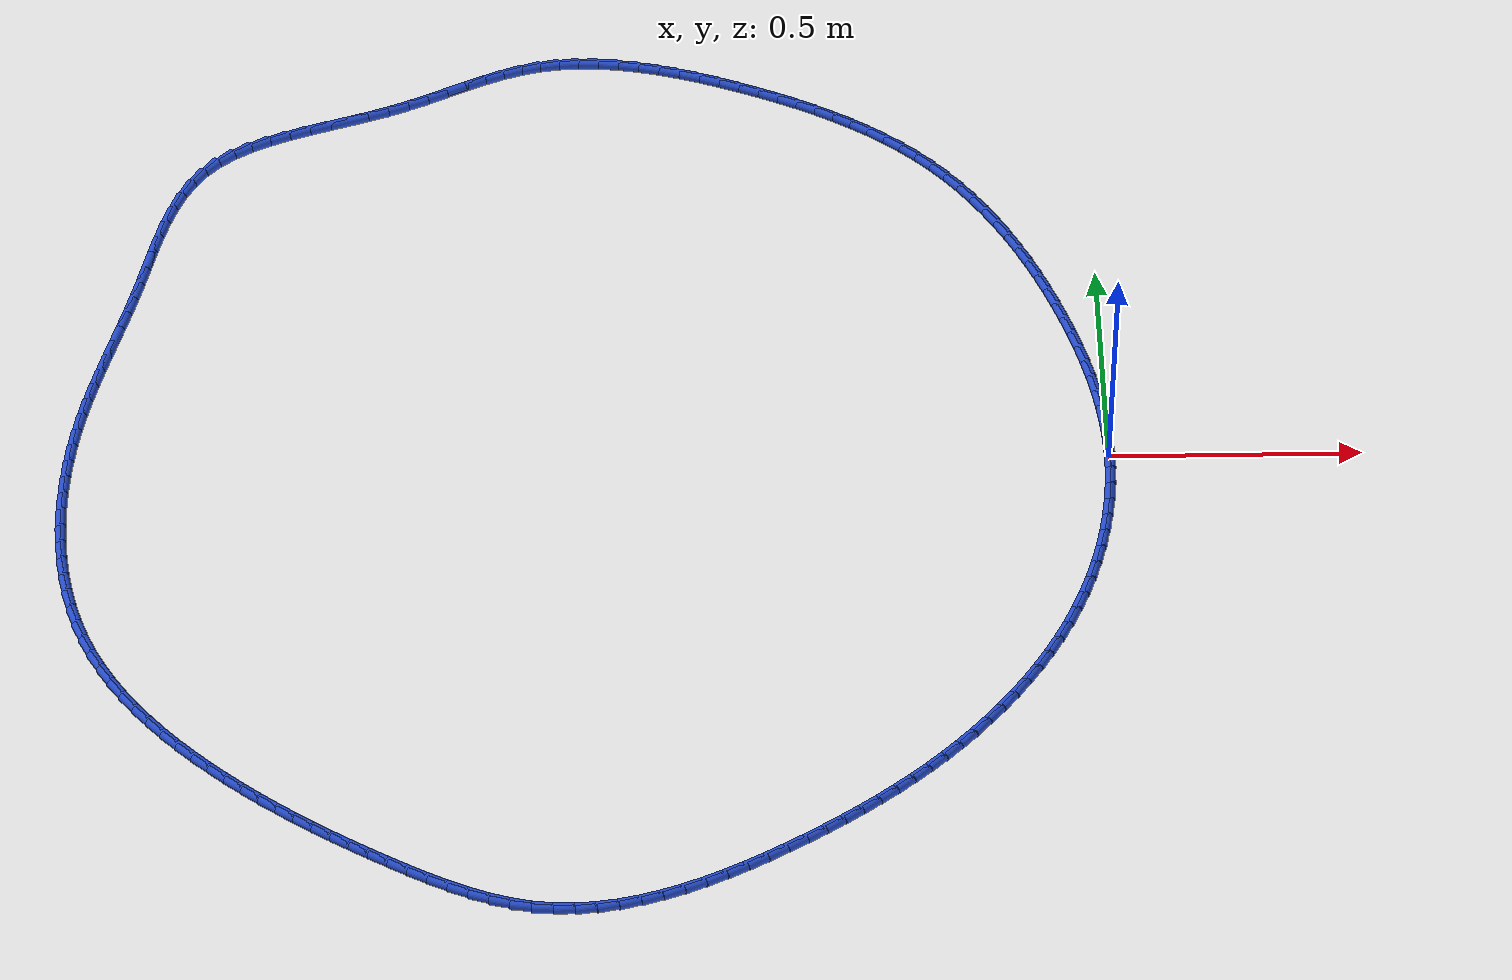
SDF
<sdf version="1.6">
 <world name="default">
  <light name="sun" type="directional">
   <pose>0 0 10 0 -0 0</pose>
   <diffuse>0.8 0.8 0.8 1</diffuse>
   <specular>0.2 0.2 0.2 1</specular>
   <attenuation>
    <range>1000</range>
    <constant>0.9</constant>
    <linear>0.01</linear>
    <quadratic>0.001</quadratic>
   </attenuation>
   <direction>-0.5 0.1 -0.9</direction>
  </light>
  <model name="ground_plane">
   <static>1</static>
   <link name="link">
    <collision name="collision">
     <geometry><plane><normal>0 0 1</normal><size>100 100</size></plane></geometry>
     <surface><friction><ode><mu>100</mu><mu2>50</mu2></ode></friction></surface>
    </collision>
    <visual name="visual">
     <cast_shadows>0</cast_shadows>
     <geometry><plane><normal>0 0 1</normal><size>100 100</size></plane></geometry>
     <material>
      <script><uri>file://media/materials/scripts/gazebo.material</uri><name>Gazebo/WhiteGlow</name></script>
     </material>
    </visual>
   </link>
  </model>
  <gravity>0 0 -9.8</gravity>
  <magnetic_field>6e-06 2.3e-05 -4.2e-05</magnetic_field>
  <atmosphere type="adiabatic"/>
  <physics name="default_physics" default="0" type="ode">
   <max_step_size>0.001</max_step_size>
   <real_time_factor>1</real_time_factor>
   <real_time_update_rate>1000</real_time_update_rate>
  </physics>
  <scene><ambient>0.4 0.4 0.4 1</ambient><background>0.7 0.7 0.7 1</background><shadows>1</shadows></scene>
  <spherical_coordinates>
   <surface_model>EARTH_WGS84</surface_model>
   <latitude_deg>0</latitude_deg>
   <longitude_deg>0</longitude_deg>
   <elevation>0</elevation>
   <heading_deg>0</heading_deg>
  </spherical_coordinates>
  <model name="line">
   <link name="link_0">
    <pose>1.3877787807814457e-17 -1.1102230246251565e-16 0.01 0 1.57 -1.5345548613819546</pose>
    <collision name="collision">
     <geometry><cylinder><radius>0.01</radius><length>0.08</length></cylinder></geometry>
    </collision>
    <visual name="visual">
     <material>
      <script><name>Gazebo/Blue</name><uri>file://media/materials/scripts/gazebo.material</uri></script>
     </material>
     <geometry><cylinder><radius>0.01</radius><length>0.08</length></cylinder></geometry>
    </visual>
   </link>
   <link name="link_1">
    <pose>-0.0014994985751226322 0.0413571029254914 0.01 0 1.57 -1.4905350404561943</pose>
    <collision name="collision">
     <geometry><cylinder><radius>0.01</radius><length>0.08</length></cylinder></geometry>
    </collision>
    <visual name="visual">
     <material>
      <script><name>Gazebo/Blue</name><uri>file://media/materials/scripts/gazebo.material</uri></script>
     </material>
     <geometry><cylinder><radius>0.01</radius><length>0.08</length></cylinder></geometry>
    </visual>
   </link>
   <link name="link_2">
    <pose>-0.004814354495690805 0.08256918724697052 0.01 0 1.57 -1.448894063524369</pose>
    <collision name="collision">
     <geometry><cylinder><radius>0.01</radius><length>0.08</length></cylinder></geometry>
    </collision>
    <visual name="visual">
     <material>
      <script><name>Gazebo/Blue</name><uri>file://media/materials/scripts/gazebo.material</uri></script>
     </material>
     <geometry><cylinder><radius>0.01</radius><length>0.08</length></cylinder></geometry>
    </visual>
   </link>
   <link name="link_3">
    <pose>-0.00984477007275671 0.12363055170432462 0.01 0 1.57 -1.40972528085246</pose>
    <collision name="collision">
     <geometry><cylinder><radius>0.01</radius><length>0.08</length></cylinder></geometry>
    </collision>
    <visual name="visual">
     <material>
      <script><name>Gazebo/Blue</name><uri>file://media/materials/scripts/gazebo.material</uri></script>
     </material>
     <geometry><cylinder><radius>0.01</radius><length>0.08</length></cylinder></geometry>
    </visual>
   </link>
   <link name="link_4">
    <pose>-0.01649094761737251 0.16453549503744083 0.01 0 1.57 -1.3730803527121769</pose>
    <collision name="collision">
     <geometry><cylinder><radius>0.01</radius><length>0.08</length></cylinder></geometry>
    </collision>
    <visual name="visual">
     <material>
      <script><name>Gazebo/Blue</name><uri>file://media/materials/scripts/gazebo.material</uri></script>
     </material>
     <geometry><cylinder><radius>0.01</radius><length>0.08</length></cylinder></geometry>
    </visual>
   </link>
   <link name="link_5">
    <pose>-0.024653089440590414 0.2052783159862065 0.01 0 1.57 -1.3389760038839054</pose>
    <collision name="collision">
     <geometry><cylinder><radius>0.01</radius><length>0.08</length></cylinder></geometry>
    </collision>
    <visual name="visual">
     <material>
      <script><name>Gazebo/Blue</name><uri>file://media/materials/scripts/gazebo.material</uri></script>
     </material>
     <geometry><cylinder><radius>0.01</radius><length>0.08</length></cylinder></geometry>
    </visual>
   </link>
   <link name="link_6">
    <pose>-0.03423139785346262 0.2458533132905088 0.01 0 1.57 -1.3074010422420275</pose>
    <collision name="collision">
     <geometry><cylinder><radius>0.01</radius><length>0.08</length></cylinder></geometry>
    </collision>
    <visual name="visual">
     <material>
      <script><name>Gazebo/Blue</name><uri>file://media/materials/scripts/gazebo.material</uri></script>
     </material>
     <geometry><cylinder><radius>0.01</radius><length>0.08</length></cylinder></geometry>
    </visual>
   </link>
   <link name="link_7">
    <pose>-0.045126075167041285 0.2862547856902349 0.01 0 1.57 -1.2783231371852053</pose>
    <collision name="collision">
     <geometry><cylinder><radius>0.01</radius><length>0.08</length></cylinder></geometry>
    </collision>
    <visual name="visual">
     <material>
      <script><name>Gazebo/Blue</name><uri>file://media/materials/scripts/gazebo.material</uri></script>
     </material>
     <geometry><cylinder><radius>0.01</radius><length>0.08</length></cylinder></geometry>
    </visual>
   </link>
   <link name="link_8">
    <pose>-0.05723732369237864 0.3264770319252721 0.01 0 1.57 -1.251695029158145</pose>
    <collision name="collision">
     <geometry><cylinder><radius>0.01</radius><length>0.08</length></cylinder></geometry>
    </collision>
    <visual name="visual">
     <material>
      <script><name>Gazebo/Blue</name><uri>file://media/materials/scripts/gazebo.material</uri></script>
     </material>
     <geometry><cylinder><radius>0.01</radius><length>0.08</length></cylinder></geometry>
    </visual>
   </link>
   <link name="link_9">
    <pose>-0.07046534574052682 0.36651435073550764 0.01 0 1.57 -1.2273121983127415</pose>
    <collision name="collision">
     <geometry><cylinder><radius>0.01</radius><length>0.08</length></cylinder></geometry>
    </collision>
    <visual name="visual">
     <material>
      <script><name>Gazebo/Blue</name><uri>file://media/materials/scripts/gazebo.material</uri></script>
     </material>
     <geometry><cylinder><radius>0.01</radius><length>0.08</length></cylinder></geometry>
    </visual>
   </link>
   <link name="link_10">
    <pose>-0.0847154783561046 0.4063568262257687 0.01 0 1.57 -1.2028412332825416</pose>
    <collision name="collision">
     <geometry><cylinder><radius>0.01</radius><length>0.08</length></cylinder></geometry>
    </collision>
    <visual name="visual">
     <material>
      <script><name>Gazebo/Blue</name><uri>file://media/materials/scripts/gazebo.material</uri></script>
     </material>
     <geometry><cylinder><radius>0.01</radius><length>0.08</length></cylinder></geometry>
    </visual>
   </link>
   <link name="link_11">
    <pose>-0.09997149352571137 0.44593016240167804 0.01 0 1.57 -1.1763962450981311</pose>
    <collision name="collision">
     <geometry><cylinder><radius>0.01</radius><length>0.08</length></cylinder></geometry>
    </collision>
    <visual name="visual">
     <material>
      <script><name>Gazebo/Blue</name><uri>file://media/materials/scripts/gazebo.material</uri></script>
     </material>
     <geometry><cylinder><radius>0.01</radius><length>0.08</length></cylinder></geometry>
    </visual>
   </link>
   <link name="link_12">
    <pose>-0.1162783736929553 0.48510982118038287 0.01 0 1.57 -1.1477853626088326</pose>
    <collision name="collision">
     <geometry><cylinder><radius>0.01</radius><length>0.08</length></cylinder></geometry>
    </collision>
    <visual name="visual">
     <material>
      <script><name>Gazebo/Blue</name><uri>file://media/materials/scripts/gazebo.material</uri></script>
     </material>
     <geometry><cylinder><radius>0.01</radius><length>0.08</length></cylinder></geometry>
    </visual>
   </link>
   <link name="link_13">
    <pose>-0.13368272460972086 0.5237699320531336 0.01 0 1.57 -1.1168529897270363</pose>
    <collision name="collision">
     <geometry><cylinder><radius>0.01</radius><length>0.08</length></cylinder></geometry>
    </collision>
    <visual name="visual">
     <material>
      <script><name>Gazebo/Blue</name><uri>file://media/materials/scripts/gazebo.material</uri></script>
     </material>
     <geometry><cylinder><radius>0.01</radius><length>0.08</length></cylinder></geometry>
    </visual>
   </link>
   <link name="link_14">
    <pose>-0.1522311520278927 0.5617846245111813 0.01 0 1.57 -1.0834355295382123</pose>
    <collision name="collision">
     <geometry><cylinder><radius>0.01</radius><length>0.08</length></cylinder></geometry>
    </collision>
    <visual name="visual">
     <material>
      <script><name>Gazebo/Blue</name><uri>file://media/materials/scripts/gazebo.material</uri></script>
     </material>
     <geometry><cylinder><radius>0.01</radius><length>0.08</length></cylinder></geometry>
    </visual>
   </link>
   <link name="link_15">
    <pose>-0.17197026169935523 0.5990280280457766 0.01 0 1.57 -1.0473650428771837</pose>
    <collision name="collision">
     <geometry><cylinder><radius>0.01</radius><length>0.08</length></cylinder></geometry>
    </collision>
    <visual name="visual">
     <material>
      <script><name>Gazebo/Blue</name><uri>file://media/materials/scripts/gazebo.material</uri></script>
     </material>
     <geometry><cylinder><radius>0.01</radius><length>0.08</length></cylinder></geometry>
    </visual>
   </link>
   <link name="link_16">
    <pose>-0.1929466593759931 0.6353742721481703 0.01 0 1.57 -1.0084744888621753</pose>
    <collision name="collision">
     <geometry><cylinder><radius>0.01</radius><length>0.08</length></cylinder></geometry>
    </collision>
    <visual name="visual">
     <material>
      <script><name>Gazebo/Blue</name><uri>file://media/materials/scripts/gazebo.material</uri></script>
     </material>
     <geometry><cylinder><radius>0.01</radius><length>0.08</length></cylinder></geometry>
    </visual>
   </link>
   <link name="link_17">
    <pose>-0.21520695080969077 0.6706974863096132 0.01 0 1.57 -0.9666049427336928</pose>
    <collision name="collision">
     <geometry><cylinder><radius>0.01</radius><length>0.08</length></cylinder></geometry>
    </collision>
    <visual name="visual">
     <material>
      <script><name>Gazebo/Blue</name><uri>file://media/materials/scripts/gazebo.material</uri></script>
     </material>
     <geometry><cylinder><radius>0.01</radius><length>0.08</length></cylinder></geometry>
    </visual>
   </link>
   <link name="link_18">
    <pose>-0.23879774175233276 0.704871800021356 0.01 0 1.57 -0.9216151532230433</pose>
    <collision name="collision">
     <geometry><cylinder><radius>0.01</radius><length>0.08</length></cylinder></geometry>
    </collision>
    <visual name="visual">
     <material>
      <script><name>Gazebo/Blue</name><uri>file://media/materials/scripts/gazebo.material</uri></script>
     </material>
     <geometry><cylinder><radius>0.01</radius><length>0.08</length></cylinder></geometry>
    </visual>
   </link>
   <link name="link_19">
    <pose>-0.26376563795580366 0.7377713427746495 0.01 0 1.57 -0.8733936760965376</pose>
    <collision name="collision">
     <geometry><cylinder><radius>0.01</radius><length>0.08</length></cylinder></geometry>
    </collision>
    <visual name="visual">
     <material>
      <script><name>Gazebo/Blue</name><uri>file://media/materials/scripts/gazebo.material</uri></script>
     </material>
     <geometry><cylinder><radius>0.01</radius><length>0.08</length></cylinder></geometry>
    </visual>
   </link>
   <link name="link_20">
    <pose>-0.2901572451719879 0.7692702440607441 0.01 0 1.57 -0.8218735560682727</pose>
    <collision name="collision">
     <geometry><cylinder><radius>0.01</radius><length>0.08</length></cylinder></geometry>
    </collision>
    <visual name="visual">
     <material>
      <script><name>Gazebo/Blue</name><uri>file://media/materials/scripts/gazebo.material</uri></script>
     </material>
     <geometry><cylinder><radius>0.01</radius><length>0.08</length></cylinder></geometry>
    </visual>
   </link>
   <link name="link_21">
    <pose>-0.3180191691527701 0.7992426333708911 0.01 0 1.57 -0.7673353651680067</pose>
    <collision name="collision">
     <geometry><cylinder><radius>0.01</radius><length>0.08</length></cylinder></geometry>
    </collision>
    <visual name="visual">
     <material>
      <script><name>Gazebo/Blue</name><uri>file://media/materials/scripts/gazebo.material</uri></script>
     </material>
     <geometry><cylinder><radius>0.01</radius><length>0.08</length></cylinder></geometry>
    </visual>
   </link>
   <link name="link_22">
    <pose>-0.3473917130122119 0.8275727915982415 0.01 0 1.57 -0.7133941890469484</pose>
    <collision name="collision">
     <geometry><cylinder><radius>0.01</radius><length>0.08</length></cylinder></geometry>
    </collision>
    <visual name="visual">
     <material>
      <script><name>Gazebo/Blue</name><uri>file://media/materials/scripts/gazebo.material</uri></script>
     </material>
     <geometry><cylinder><radius>0.01</radius><length>0.08</length></cylinder></geometry>
    </visual>
   </link>
   <link name="link_23">
    <pose>-0.3782382702803706 0.8542688747687301 0.01 0 1.57 -0.6626493005035978</pose>
    <collision name="collision">
     <geometry><cylinder><radius>0.01</radius><length>0.08</length></cylinder></geometry>
    </collision>
    <visual name="visual">
     <material>
      <script><name>Gazebo/Blue</name><uri>file://media/materials/scripts/gazebo.material</uri></script>
     </material>
     <geometry><cylinder><radius>0.01</radius><length>0.08</length></cylinder></geometry>
    </visual>
   </link>
   <link name="link_24">
    <pose>-0.4104708297316704 0.879421834453376 0.01 0 1.57 -0.6153462506921251</pose>
    <collision name="collision">
     <geometry><cylinder><radius>0.01</radius><length>0.08</length></cylinder></geometry>
    </collision>
    <visual name="visual">
     <material>
      <script><name>Gazebo/Blue</name><uri>file://media/materials/scripts/gazebo.material</uri></script>
     </material>
     <geometry><cylinder><radius>0.01</radius><length>0.08</length></cylinder></geometry>
    </visual>
   </link>
   <link name="link_25">
    <pose>-0.44400043947456364 0.9031241373155454 0.01 0 1.57 -0.5715967147624706</pose>
    <collision name="collision">
     <geometry><cylinder><radius>0.01</radius><length>0.08</length></cylinder></geometry>
    </collision>
    <visual name="visual">
     <material>
      <script><name>Gazebo/Blue</name><uri>file://media/materials/scripts/gazebo.material</uri></script>
     </material>
     <geometry><cylinder><radius>0.01</radius><length>0.08</length></cylinder></geometry>
    </visual>
   </link>
   <link name="link_26">
    <pose>-0.4787381476175033 0.9254682500186047 0.01 0 1.57 -0.5314364706690613</pose>
    <collision name="collision">
     <geometry><cylinder><radius>0.01</radius><length>0.08</length></cylinder></geometry>
    </collision>
    <visual name="visual">
     <material>
      <script><name>Gazebo/Blue</name><uri>file://media/materials/scripts/gazebo.material</uri></script>
     </material>
     <geometry><cylinder><radius>0.01</radius><length>0.08</length></cylinder></geometry>
    </visual>
   </link>
   <link name="link_27">
    <pose>-0.5145950022689415 0.94654663922592 0.01 0 1.57 -0.4948420072376537</pose>
    <collision name="collision">
     <geometry><cylinder><radius>0.01</radius><length>0.08</length></cylinder></geometry>
    </collision>
    <visual name="visual">
     <material>
      <script><name>Gazebo/Blue</name><uri>file://media/materials/scripts/gazebo.material</uri></script>
     </material>
     <geometry><cylinder><radius>0.01</radius><length>0.08</length></cylinder></geometry>
    </visual>
   </link>
   <link name="link_28">
    <pose>-0.551482051537331 0.9664517716008574 0.01 0 1.57 -0.4617466182630546</pose>
    <collision name="collision">
     <geometry><cylinder><radius>0.01</radius><length>0.08</length></cylinder></geometry>
    </collision>
    <visual name="visual">
     <material>
      <script><name>Gazebo/Blue</name><uri>file://media/materials/scripts/gazebo.material</uri></script>
     </material>
     <geometry><cylinder><radius>0.01</radius><length>0.08</length></cylinder></geometry>
    </visual>
   </link>
   <link name="link_29">
    <pose>-0.5893103435311241 0.9852761138067833 0.01 0 1.57 -0.432054821529806</pose>
    <collision name="collision">
     <geometry><cylinder><radius>0.01</radius><length>0.08</length></cylinder></geometry>
    </collision>
    <visual name="visual">
     <material>
      <script><name>Gazebo/Blue</name><uri>file://media/materials/scripts/gazebo.material</uri></script>
     </material>
     <geometry><cylinder><radius>0.01</radius><length>0.08</length></cylinder></geometry>
    </visual>
   </link>
   <link name="link_30">
    <pose>-0.6279909263587731 1.0031121325070633 0.01 0 1.57 -0.40565454657202965</pose>
    <collision name="collision">
     <geometry><cylinder><radius>0.01</radius><length>0.08</length></cylinder></geometry>
    </collision>
    <visual name="visual">
     <material>
      <script><name>Gazebo/Blue</name><uri>file://media/materials/scripts/gazebo.material</uri></script>
     </material>
     <geometry><cylinder><radius>0.01</radius><length>0.08</length></cylinder></geometry>
    </visual>
   </link>
   <link name="link_31">
    <pose>-0.667434848128731 1.0200522943650643 0.01 0 1.57 -0.38241852478446453</pose>
    <collision name="collision">
     <geometry><cylinder><radius>0.01</radius><length>0.08</length></cylinder></geometry>
    </collision>
    <visual name="visual">
     <material>
      <script><name>Gazebo/Blue</name><uri>file://media/materials/scripts/gazebo.material</uri></script>
     </material>
     <geometry><cylinder><radius>0.01</radius><length>0.08</length></cylinder></geometry>
    </visual>
   </link>
   <link name="link_32">
    <pose>-0.7075531037622501 1.03618865079468 0.01 0 1.57 -0.3600184804603208</pose>
    <collision name="collision">
     <geometry><cylinder><radius>0.01</radius><length>0.08</length></cylinder></geometry>
    </collision>
    <visual name="visual">
     <material>
      <script><name>Gazebo/Blue</name><uri>file://media/materials/scripts/gazebo.material</uri></script>
     </material>
     <geometry><cylinder><radius>0.01</radius><length>0.08</length></cylinder></geometry>
    </visual>
   </link>
   <link name="link_33">
    <pose>-0.7482428542671798 1.0515052474264046 0.01 0 1.57 -0.3330985027308311</pose>
    <collision name="collision">
     <geometry><cylinder><radius>0.01</radius><length>0.08</length></cylinder></geometry>
    </collision>
    <visual name="visual">
     <material>
      <script><name>Gazebo/Blue</name><uri>file://media/materials/scripts/gazebo.material</uri></script>
     </material>
     <geometry><cylinder><radius>0.01</radius><length>0.08</length></cylinder></geometry>
    </visual>
   </link>
   <link name="link_34">
    <pose>-0.7893690329723269 1.0657345181001185 0.01 0 1.57 -0.30055069973156906</pose>
    <collision name="collision">
     <geometry><cylinder><radius>0.01</radius><length>0.08</length></cylinder></geometry>
    </collision>
    <visual name="visual">
     <material>
      <script><name>Gazebo/Blue</name><uri>file://media/materials/scripts/gazebo.material</uri></script>
     </material>
     <geometry><cylinder><radius>0.01</radius><length>0.08</length></cylinder></geometry>
    </visual>
   </link>
   <link name="link_35">
    <pose>-0.8307919933168675 1.078573139993577 0.01 0 1.57 -0.2618733742296081</pose>
    <collision name="collision">
     <geometry><cylinder><radius>0.01</radius><length>0.08</length></cylinder></geometry>
    </collision>
    <visual name="visual">
     <material>
      <script><name>Gazebo/Blue</name><uri>file://media/materials/scripts/gazebo.material</uri></script>
     </material>
     <geometry><cylinder><radius>0.01</radius><length>0.08</length></cylinder></geometry>
    </visual>
   </link>
   <link name="link_36">
    <pose>-0.8723720887399773 1.0897177902845347 0.01 0 1.57 -0.2164560009047103</pose>
    <collision name="collision">
     <geometry><cylinder><radius>0.01</radius><length>0.08</length></cylinder></geometry>
    </collision>
    <visual name="visual">
     <material>
      <script><name>Gazebo/Blue</name><uri>file://media/materials/scripts/gazebo.material</uri></script>
     </material>
     <geometry><cylinder><radius>0.01</radius><length>0.08</length></cylinder></geometry>
    </visual>
   </link>
   <link name="link_37">
    <pose>-0.9139696726808327 1.0988651461507475 0.01 0 1.57 -0.16360391809180144</pose>
    <collision name="collision">
     <geometry><cylinder><radius>0.01</radius><length>0.08</length></cylinder></geometry>
    </collision>
    <visual name="visual">
     <material>
      <script><name>Gazebo/Blue</name><uri>file://media/materials/scripts/gazebo.material</uri></script>
     </material>
     <geometry><cylinder><radius>0.01</radius><length>0.08</length></cylinder></geometry>
    </visual>
   </link>
   <link name="link_38">
    <pose>-0.9554450985786102 1.1057118847699696 0.01 0 1.57 -0.10258513177906603</pose>
    <collision name="collision">
     <geometry><cylinder><radius>0.01</radius><length>0.08</length></cylinder></geometry>
    </collision>
    <visual name="visual">
     <material>
      <script><name>Gazebo/Blue</name><uri>file://media/materials/scripts/gazebo.material</uri></script>
     </material>
     <geometry><cylinder><radius>0.01</radius><length>0.08</length></cylinder></geometry>
    </visual>
   </link>
   <link name="link_39">
    <pose>-0.996658719872485 1.1099546833199565 0.01 0 1.57 -0.03271228257768175</pose>
    <collision name="collision">
     <geometry><cylinder><radius>0.01</radius><length>0.08</length></cylinder></geometry>
    </collision>
    <visual name="visual">
     <material>
      <script><name>Gazebo/Blue</name><uri>file://media/materials/scripts/gazebo.material</uri></script>
     </material>
     <geometry><cylinder><radius>0.01</radius><length>0.08</length></cylinder></geometry>
    </visual>
   </link>
   <link name="link_40">
    <pose>-1.037470890001634 1.1112902189784633 0.01 0 1.57 0.04652711559829884</pose>
    <collision name="collision">
     <geometry><cylinder><radius>0.01</radius><length>0.08</length></cylinder></geometry>
    </collision>
    <visual name="visual">
     <material>
      <script><name>Gazebo/Blue</name><uri>file://media/materials/scripts/gazebo.material</uri></script>
     </material>
     <geometry><cylinder><radius>0.01</radius><length>0.08</length></cylinder></geometry>
    </visual>
   </link>
   <link name="link_41">
    <pose>-1.0777419624052331 1.109415168923245 0.01 0 1.57 0.13528661117962762</pose>
    <collision name="collision">
     <geometry><cylinder><radius>0.01</radius><length>0.08</length></cylinder></geometry>
    </collision>
    <visual name="visual">
     <material>
      <script><name>Gazebo/Blue</name><uri>file://media/materials/scripts/gazebo.material</uri></script>
     </material>
     <geometry><cylinder><radius>0.01</radius><length>0.08</length></cylinder></geometry>
    </visual>
   </link>
   <link name="link_42">
    <pose>-1.1173322905224579 1.1040262103320568 0.01 0 1.57 0.23039331265800722</pose>
    <collision name="collision">
     <geometry><cylinder><radius>0.01</radius><length>0.08</length></cylinder></geometry>
    </collision>
    <visual name="visual">
     <material>
      <script><name>Gazebo/Blue</name><uri>file://media/materials/scripts/gazebo.material</uri></script>
     </material>
     <geometry><cylinder><radius>0.01</radius><length>0.08</length></cylinder></geometry>
    </visual>
   </link>
   <link name="link_43">
    <pose>-1.1561430776383477 1.0949228190211655 0.01 0 1.57 0.3124875136861646</pose>
    <collision name="collision">
     <geometry><cylinder><radius>0.01</radius><length>0.08</length></cylinder></geometry>
    </collision>
    <visual name="visual">
     <material>
      <script><name>Gazebo/Blue</name><uri>file://media/materials/scripts/gazebo.material</uri></script>
     </material>
     <geometry><cylinder><radius>0.01</radius><length>0.08</length></cylinder></geometry>
    </visual>
   </link>
   <link name="link_44">
    <pose>-1.1943443769005473 1.082581031495295 0.01 0 1.57 0.37325666811087105</pose>
    <collision name="collision">
     <geometry><cylinder><radius>0.01</radius><length>0.08</length></cylinder></geometry>
    </collision>
    <visual name="visual">
     <material>
      <script><name>Gazebo/Blue</name><uri>file://media/materials/scripts/gazebo.material</uri></script>
     </material>
     <geometry><cylinder><radius>0.01</radius><length>0.08</length></cylinder></geometry>
    </visual>
   </link>
   <link name="link_45">
    <pose>-1.232214921234384 1.067750376923432 0.01 0 1.57 0.41293162421717494</pose>
    <collision name="collision">
     <geometry><cylinder><radius>0.01</radius><length>0.08</length></cylinder></geometry>
    </collision>
    <visual name="visual">
     <material>
      <script><name>Gazebo/Blue</name><uri>file://media/materials/scripts/gazebo.material</uri></script>
     </material>
     <geometry><cylinder><radius>0.01</radius><length>0.08</length></cylinder></geometry>
    </visual>
   </link>
   <link name="link_46">
    <pose>-1.270033748351906 1.0511811514703508 0.01 0 1.57 0.43235879861497617</pose>
    <collision name="collision">
     <geometry><cylinder><radius>0.01</radius><length>0.08</length></cylinder></geometry>
    </collision>
    <visual name="visual">
     <material>
      <script><name>Gazebo/Blue</name><uri>file://media/materials/scripts/gazebo.material</uri></script>
     </material>
     <geometry><cylinder><radius>0.01</radius><length>0.08</length></cylinder></geometry>
    </visual>
   </link>
   <link name="link_47">
    <pose>-1.3080798959651592 1.033623651300827 0.01 0 1.57 0.4324508518343912</pose>
    <collision name="collision">
     <geometry><cylinder><radius>0.01</radius><length>0.08</length></cylinder></geometry>
    </collision>
    <visual name="visual">
     <material>
      <script><name>Gazebo/Blue</name><uri>file://media/materials/scripts/gazebo.material</uri></script>
     </material>
     <geometry><cylinder><radius>0.01</radius><length>0.08</length></cylinder></geometry>
    </visual>
   </link>
   <link name="link_48">
    <pose>-1.3466324017861915 1.0158281725796348 0.01 0 1.57 0.4139633232318281</pose>
    <collision name="collision">
     <geometry><cylinder><radius>0.01</radius><length>0.08</length></cylinder></geometry>
    </collision>
    <visual name="visual">
     <material>
      <script><name>Gazebo/Blue</name><uri>file://media/materials/scripts/gazebo.material</uri></script>
     </material>
     <geometry><cylinder><radius>0.01</radius><length>0.08</length></cylinder></geometry>
    </visual>
   </link>
   <link name="link_49">
    <pose>-1.3859703035270494 0.9985450114715495 0.01 0 1.57 0.3776107500835675</pose>
    <collision name="collision">
     <geometry><cylinder><radius>0.01</radius><length>0.08</length></cylinder></geometry>
    </collision>
    <visual name="visual">
     <material>
      <script><name>Gazebo/Blue</name><uri>file://media/materials/scripts/gazebo.material</uri></script>
     </material>
     <geometry><cylinder><radius>0.01</radius><length>0.08</length></cylinder></geometry>
    </visual>
   </link>
   <link name="link_50">
    <pose>-1.4263702786159698 0.9825205654023055 0.01 0 1.57 0.33534078591751243</pose>
    <collision name="collision">
     <geometry><cylinder><radius>0.01</radius><length>0.08</length></cylinder></geometry>
    </collision>
    <visual name="visual">
     <material>
      <script><name>Gazebo/Blue</name><uri>file://media/materials/scripts/gazebo.material</uri></script>
     </material>
     <geometry><cylinder><radius>0.01</radius><length>0.08</length></cylinder></geometry>
    </visual>
   </link>
   <link name="link_51">
    <pose>-1.467845671740134 0.9680662562944938 0.01 0 1.57 0.30836272072563947</pose>
    <collision name="collision">
     <geometry><cylinder><radius>0.01</radius><length>0.08</length></cylinder></geometry>
    </collision>
    <visual name="visual">
     <material>
      <script><name>Gazebo/Blue</name><uri>file://media/materials/scripts/gazebo.material</uri></script>
     </material>
     <geometry><cylinder><radius>0.01</radius><length>0.08</length></cylinder></geometry>
    </visual>
   </link>
   <link name="link_52">
    <pose>-1.509909952785031 0.9546678081627891 0.01 0 1.57 0.29832438738879186</pose>
    <collision name="collision">
     <geometry><cylinder><radius>0.01</radius><length>0.08</length></cylinder></geometry>
    </collision>
    <visual name="visual">
     <material>
      <script><name>Gazebo/Blue</name><uri>file://media/materials/scripts/gazebo.material</uri></script>
     </material>
     <geometry><cylinder><radius>0.01</radius><length>0.08</length></cylinder></geometry>
    </visual>
   </link>
   <link name="link_53">
    <pose>-1.5520207398676904 0.9417186885444131 0.01 0 1.57 0.3051089379654529</pose>
    <collision name="collision">
     <geometry><cylinder><radius>0.01</radius><length>0.08</length></cylinder></geometry>
    </collision>
    <visual name="visual">
     <material>
      <script><name>Gazebo/Blue</name><uri>file://media/materials/scripts/gazebo.material</uri></script>
     </material>
     <geometry><cylinder><radius>0.01</radius><length>0.08</length></cylinder></geometry>
    </visual>
   </link>
   <link name="link_54">
    <pose>-1.593635651105139 0.9286123649765872 0.01 0 1.57 0.32937228199061636</pose>
    <collision name="collision">
     <geometry><cylinder><radius>0.01</radius><length>0.08</length></cylinder></geometry>
    </collision>
    <visual name="visual">
     <material>
      <script><name>Gazebo/Blue</name><uri>file://media/materials/scripts/gazebo.material</uri></script>
     </material>
     <geometry><cylinder><radius>0.01</radius><length>0.08</length></cylinder></geometry>
    </visual>
   </link>
   <link name="link_55">
    <pose>-1.6342123046144061 0.9147423049965333 0.01 0 1.57 0.3725655445291035</pose>
    <collision name="collision">
     <geometry><cylinder><radius>0.01</radius><length>0.08</length></cylinder></geometry>
    </collision>
    <visual name="visual">
     <material>
      <script><name>Gazebo/Blue</name><uri>file://media/materials/scripts/gazebo.material</uri></script>
     </material>
     <geometry><cylinder><radius>0.01</radius><length>0.08</length></cylinder></geometry>
    </visual>
   </link>
   <link name="link_56">
    <pose>-1.67320831851252 0.8995019761414726 0.01 0 1.57 0.43684390989538824</pose>
    <collision name="collision">
     <geometry><cylinder><radius>0.01</radius><length>0.08</length></cylinder></geometry>
    </collision>
    <visual name="visual">
     <material>
      <script><name>Gazebo/Blue</name><uri>file://media/materials/scripts/gazebo.material</uri></script>
     </material>
     <geometry><cylinder><radius>0.01</radius><length>0.08</length></cylinder></geometry>
    </visual>
   </link>
   <link name="link_57">
    <pose>-1.7100813109165087 0.8822848459486273 0.01 0 1.57 0.5247097290324274</pose>
    <collision name="collision">
     <geometry><cylinder><radius>0.01</radius><length>0.08</length></cylinder></geometry>
    </collision>
    <visual name="visual">
     <material>
      <script><name>Gazebo/Blue</name><uri>file://media/materials/scripts/gazebo.material</uri></script>
     </material>
     <geometry><cylinder><radius>0.01</radius><length>0.08</length></cylinder></geometry>
    </visual>
   </link>
   <link name="link_58">
    <pose>-1.7442888999434014 0.8624843819552186 0.01 0 1.57 0.6381216241457354</pose>
    <collision name="collision">
     <geometry><cylinder><radius>0.01</radius><length>0.08</length></cylinder></geometry>
    </collision>
    <visual name="visual">
     <material>
      <script><name>Gazebo/Blue</name><uri>file://media/materials/scripts/gazebo.material</uri></script>
     </material>
     <geometry><cylinder><radius>0.01</radius><length>0.08</length></cylinder></geometry>
    </visual>
   </link>
   <link name="link_59">
    <pose>-1.7752887037102258 0.8394940516984681 0.01 0 1.57 0.7767245210007024</pose>
    <collision name="collision">
     <geometry><cylinder><radius>0.01</radius><length>0.08</length></cylinder></geometry>
    </collision>
    <visual name="visual">
     <material>
      <script><name>Gazebo/Blue</name><uri>file://media/materials/scripts/gazebo.material</uri></script>
     </material>
     <geometry><cylinder><radius>0.01</radius><length>0.08</length></cylinder></geometry>
    </visual>
   </link>
   <link name="link_60">
    <pose>-1.8025410959293975 0.8127103608938179 0.01 0 1.57 0.9229240602292601</pose>
    <collision name="collision">
     <geometry><cylinder><radius>0.01</radius><length>0.08</length></cylinder></geometry>
    </collision>
    <visual name="visual">
     <material>
      <script><name>Gazebo/Blue</name><uri>file://media/materials/scripts/gazebo.material</uri></script>
     </material>
     <geometry><cylinder><radius>0.01</radius><length>0.08</length></cylinder></geometry>
    </visual>
   </link>
   <link name="link_61">
    <pose>-1.8258519009762086 0.7819106914496315 0.01 0 1.57 1.0460079330104235</pose>
    <collision name="collision">
     <geometry><cylinder><radius>0.01</radius><length>0.08</length></cylinder></geometry>
    </collision>
    <visual name="visual">
     <material>
      <script><name>Gazebo/Blue</name><uri>file://media/materials/scripts/gazebo.material</uri></script>
     </material>
     <geometry><cylinder><radius>0.01</radius><length>0.08</length></cylinder></geometry>
    </visual>
   </link>
   <link name="link_62">
    <pose>-1.8457044259619007 0.7476193830108421 0.01 0 1.57 1.1428306513928117</pose>
    <collision name="collision">
     <geometry><cylinder><radius>0.01</radius><length>0.08</length></cylinder></geometry>
    </collision>
    <visual name="visual">
     <material>
      <script><name>Gazebo/Blue</name><uri>file://media/materials/scripts/gazebo.material</uri></script>
     </material>
     <geometry><cylinder><radius>0.01</radius><length>0.08</length></cylinder></geometry>
    </visual>
   </link>
   <link name="link_63">
    <pose>-1.8626607407265683 0.7104476149697982 0.01 0 1.57 1.2157701263513419</pose>
    <collision name="collision">
     <geometry><cylinder><radius>0.01</radius><length>0.08</length></cylinder></geometry>
    </collision>
    <visual name="visual">
     <material>
      <script><name>Gazebo/Blue</name><uri>file://media/materials/scripts/gazebo.material</uri></script>
     </material>
     <geometry><cylinder><radius>0.01</radius><length>0.08</length></cylinder></geometry>
    </visual>
   </link>
   <link name="link_64">
    <pose>-1.8772829151103054 0.6710065667188511 0.01 0 1.57 1.267764727014938</pose>
    <collision name="collision">
     <geometry><cylinder><radius>0.01</radius><length>0.08</length></cylinder></geometry>
    </collision>
    <visual name="visual">
     <material>
      <script><name>Gazebo/Blue</name><uri>file://media/materials/scripts/gazebo.material</uri></script>
     </material>
     <geometry><cylinder><radius>0.01</radius><length>0.08</length></cylinder></geometry>
    </visual>
   </link>
   <link name="link_65">
    <pose>-1.890133018953206 0.6299074176503496 0.01 0 1.57 1.3013289707779223</pose>
    <collision name="collision">
     <geometry><cylinder><radius>0.01</radius><length>0.08</length></cylinder></geometry>
    </collision>
    <visual name="visual">
     <material>
      <script><name>Gazebo/Blue</name><uri>file://media/materials/scripts/gazebo.material</uri></script>
     </material>
     <geometry><cylinder><radius>0.01</radius><length>0.08</length></cylinder></geometry>
    </visual>
   </link>
   <link name="link_66">
    <pose>-1.9017731220953653 0.5877613471566439 0.01 0 1.57 1.31816900950766</pose>
    <collision name="collision">
     <geometry><cylinder><radius>0.01</radius><length>0.08</length></cylinder></geometry>
    </collision>
    <visual name="visual">
     <material>
      <script><name>Gazebo/Blue</name><uri>file://media/materials/scripts/gazebo.material</uri></script>
     </material>
     <geometry><cylinder><radius>0.01</radius><length>0.08</length></cylinder></geometry>
    </visual>
   </link>
   <link name="link_67">
    <pose>-1.9127652943768765 0.545179534630084 0.01 0 1.57 1.319066214468314</pose>
    <collision name="collision">
     <geometry><cylinder><radius>0.01</radius><length>0.08</length></cylinder></geometry>
    </collision>
    <visual name="visual">
     <material>
      <script><name>Gazebo/Blue</name><uri>file://media/materials/scripts/gazebo.material</uri></script>
     </material>
     <geometry><cylinder><radius>0.01</radius><length>0.08</length></cylinder></geometry>
    </visual>
   </link>
   <link name="link_68">
    <pose>-1.923671605637834 0.5027731594630191 0.01 0 1.57 1.3050130610080215</pose>
    <collision name="collision">
     <geometry><cylinder><radius>0.01</radius><length>0.08</length></cylinder></geometry>
    </collision>
    <visual name="visual">
     <material>
      <script><name>Gazebo/Blue</name><uri>file://media/materials/scripts/gazebo.material</uri></script>
     </material>
     <geometry><cylinder><radius>0.01</radius><length>0.08</length></cylinder></geometry>
    </visual>
   </link>
   <link name="link_69">
    <pose>-1.9350130735118578 0.4611108483672182 0.01 0 1.57 1.2881803336847146</pose>
    <collision name="collision">
     <geometry><cylinder><radius>0.01</radius><length>0.08</length></cylinder></geometry>
    </collision>
    <visual name="visual">
     <material>
      <script><name>Gazebo/Blue</name><uri>file://media/materials/scripts/gazebo.material</uri></script>
     </material>
     <geometry><cylinder><radius>0.01</radius><length>0.08</length></cylinder></geometry>
    </visual>
   </link>
   <link name="link_70">
    <pose>-1.9468644708537663 0.42029867285548117 0.01 0 1.57 1.2765918486878378</pose>
    <collision name="collision">
     <geometry><cylinder><radius>0.01</radius><length>0.08</length></cylinder></geometry>
    </collision>
    <visual name="visual">
     <material>
      <script><name>Gazebo/Blue</name><uri>file://media/materials/scripts/gazebo.material</uri></script>
     </material>
     <geometry><cylinder><radius>0.01</radius><length>0.08</length></cylinder></geometry>
    </visual>
   </link>
   <link name="link_71">
    <pose>-1.9590267326370459 0.3801588576782466 0.01 0 1.57 1.2706787291060937</pose>
    <collision name="collision">
     <geometry><cylinder><radius>0.01</radius><length>0.08</length></cylinder></geometry>
    </collision>
    <visual name="visual">
     <material>
      <script><name>Gazebo/Blue</name><uri>file://media/materials/scripts/gazebo.material</uri></script>
     </material>
     <geometry><cylinder><radius>0.01</radius><length>0.08</length></cylinder></geometry>
    </visual>
   </link>
   <link name="link_72">
    <pose>-1.9712968219937526 0.34050951057217416 0.01 0 1.57 1.2706721375900754</pose>
    <collision name="collision">
     <geometry><cylinder><radius>0.01</radius><length>0.08</length></cylinder></geometry>
    </collision>
    <visual name="visual">
     <material>
      <script><name>Gazebo/Blue</name><uri>file://media/materials/scripts/gazebo.material</uri></script>
     </material>
     <geometry><cylinder><radius>0.01</radius><length>0.08</length></cylinder></geometry>
    </visual>
   </link>
   <link name="link_73">
    <pose>-1.9834717020559416 0.3011687392739223 0.01 0 1.57 1.276711785862021</pose>
    <collision name="collision">
     <geometry><cylinder><radius>0.01</radius><length>0.08</length></cylinder></geometry>
    </collision>
    <visual name="visual">
     <material>
      <script><name>Gazebo/Blue</name><uri>file://media/materials/scripts/gazebo.material</uri></script>
     </material>
     <geometry><cylinder><radius>0.01</radius><length>0.08</length></cylinder></geometry>
    </visual>
   </link>
   <link name="link_74">
    <pose>-1.9953483359556694 0.26195465152015096 0.01 0 1.57 1.2888383096005958</pose>
    <collision name="collision">
     <geometry><cylinder><radius>0.01</radius><length>0.08</length></cylinder></geometry>
    </collision>
    <visual name="visual">
     <material>
      <script><name>Gazebo/Blue</name><uri>file://media/materials/scripts/gazebo.material</uri></script>
     </material>
     <geometry><cylinder><radius>0.01</radius><length>0.08</length></cylinder></geometry>
    </visual>
   </link>
   <link name="link_75">
    <pose>-2.0067236868249916 0.22268535504751882 0.01 0 1.57 1.306982961210119</pose>
    <collision name="collision">
     <geometry><cylinder><radius>0.01</radius><length>0.08</length></cylinder></geometry>
    </collision>
    <visual name="visual">
     <material>
      <script><name>Gazebo/Blue</name><uri>file://media/materials/scripts/gazebo.material</uri></script>
     </material>
     <geometry><cylinder><radius>0.01</radius><length>0.08</length></cylinder></geometry>
    </visual>
   </link>
   <link name="link_76">
    <pose>-2.017394717795965 0.18317895759268482 0.01 0 1.57 1.3309555092560899</pose>
    <collision name="collision">
     <geometry><cylinder><radius>0.01</radius><length>0.08</length></cylinder></geometry>
    </collision>
    <visual name="visual">
     <material>
      <script><name>Gazebo/Blue</name><uri>file://media/materials/scripts/gazebo.material</uri></script>
     </material>
     <geometry><cylinder><radius>0.01</radius><length>0.08</length></cylinder></geometry>
    </visual>
   </link>
   <link name="link_77">
    <pose>-2.027158392000643 0.14325356689230875 0.01 0 1.57 1.3604179852585307</pose>
    <collision name="collision">
     <geometry><cylinder><radius>0.01</radius><length>0.08</length></cylinder></geometry>
    </collision>
    <visual name="visual">
     <material>
      <script><name>Gazebo/Blue</name><uri>file://media/materials/scripts/gazebo.material</uri></script>
     </material>
     <geometry><cylinder><radius>0.01</radius><length>0.08</length></cylinder></geometry>
    </visual>
   </link>
   <link name="link_78">
    <pose>-2.0358120709440377 0.10272832684516593 0.01 0 1.57 1.3935346851221124</pose>
    <collision name="collision">
     <geometry><cylinder><radius>0.01</radius><length>0.08</length></cylinder></geometry>
    </collision>
    <visual name="visual">
     <material>
      <script><name>Gazebo/Blue</name><uri>file://media/materials/scripts/gazebo.material</uri></script>
     </material>
     <geometry><cylinder><radius>0.01</radius><length>0.08</length></cylinder></geometry>
    </visual>
   </link>
   <link name="link_79">
    <pose>-2.043193076877486 0.0615263186558906 0.01 0 1.57 1.4276597046844424</pose>
    <collision name="collision">
     <geometry><cylinder><radius>0.01</radius><length>0.08</length></cylinder></geometry>
    </collision>
    <visual name="visual">
     <material>
      <script><name>Gazebo/Blue</name><uri>file://media/materials/scripts/gazebo.material</uri></script>
     </material>
     <geometry><cylinder><radius>0.01</radius><length>0.08</length></cylinder></geometry>
    </visual>
   </link>
   <link name="link_80">
    <pose>-2.0492122619259603 0.01976187363496415 0.01 0 1.57 1.462759148050959</pose>
    <collision name="collision">
     <geometry><cylinder><radius>0.01</radius><length>0.08</length></cylinder></geometry>
    </collision>
    <visual name="visual">
     <material>
      <script><name>Gazebo/Blue</name><uri>file://media/materials/scripts/gazebo.material</uri></script>
     </material>
     <geometry><cylinder><radius>0.01</radius><length>0.08</length></cylinder></geometry>
    </visual>
   </link>
   <link name="link_81">
    <pose>-2.0537883834736905 -0.022430115445571715 0.01 0 1.57 1.4990861172074257</pose>
    <collision name="collision">
     <geometry><cylinder><radius>0.01</radius><length>0.08</length></cylinder></geometry>
    </collision>
    <visual name="visual">
     <material>
      <script><name>Gazebo/Blue</name><uri>file://media/materials/scripts/gazebo.material</uri></script>
     </material>
     <geometry><cylinder><radius>0.01</radius><length>0.08</length></cylinder></geometry>
    </visual>
   </link>
   <link name="link_82">
    <pose>-2.0568401989049088 -0.064914755813676 0.01 0 1.57 1.5368931560237917</pose>
    <collision name="collision">
     <geometry><cylinder><radius>0.01</radius><length>0.08</length></cylinder></geometry>
    </collision>
    <visual name="visual">
     <material>
      <script><name>Gazebo/Blue</name><uri>file://media/materials/scripts/gazebo.material</uri></script>
     </material>
     <geometry><cylinder><radius>0.01</radius><length>0.08</length></cylinder></geometry>
    </visual>
   </link>
   <link name="link_83">
    <pose>-2.058286465603844 -0.10755715469730551 0.01 0 1.57 -1.5651589048027394</pose>
    <collision name="collision">
     <geometry><cylinder><radius>0.01</radius><length>0.08</length></cylinder></geometry>
    </collision>
    <visual name="visual">
     <material>
      <script><name>Gazebo/Blue</name><uri>file://media/materials/scripts/gazebo.material</uri></script>
     </material>
     <geometry><cylinder><radius>0.01</radius><length>0.08</length></cylinder></geometry>
    </visual>
   </link>
   <link name="link_84">
    <pose>-2.0580459409547287 -0.15022241932441924 0.01 0 1.57 -1.523630257499338</pose>
    <collision name="collision">
     <geometry><cylinder><radius>0.01</radius><length>0.08</length></cylinder></geometry>
    </collision>
    <visual name="visual">
     <material>
      <script><name>Gazebo/Blue</name><uri>file://media/materials/scripts/gazebo.material</uri></script>
     </material>
     <geometry><cylinder><radius>0.01</radius><length>0.08</length></cylinder></geometry>
    </visual>
   </link>
   <link name="link_85">
    <pose>-2.0560373823417932 -0.1927756569229756 0.01 0 1.57 -1.4798596668916062</pose>
    <collision name="collision">
     <geometry><cylinder><radius>0.01</radius><length>0.08</length></cylinder></geometry>
    </collision>
    <visual name="visual">
     <material>
      <script><name>Gazebo/Blue</name><uri>file://media/materials/scripts/gazebo.material</uri></script>
     </material>
     <geometry><cylinder><radius>0.01</radius><length>0.08</length></cylinder></geometry>
    </visual>
   </link>
   <link name="link_86">
    <pose>-2.0521795471492683 -0.23508197472093287 0.01 0 1.57 -1.4335975769318752</pose>
    <collision name="collision">
     <geometry><cylinder><radius>0.01</radius><length>0.08</length></cylinder></geometry>
    </collision>
    <visual name="visual">
     <material>
      <script><name>Gazebo/Blue</name><uri>file://media/materials/scripts/gazebo.material</uri></script>
     </material>
     <geometry><cylinder><radius>0.01</radius><length>0.08</length></cylinder></geometry>
    </visual>
   </link>
   <link name="link_87">
    <pose>-2.0463911927613845 -0.27700647994625 0.01 0 1.57 -1.3846050494945537</pose>
    <collision name="collision">
     <geometry><cylinder><radius>0.01</radius><length>0.08</length></cylinder></geometry>
    </collision>
    <visual name="visual">
     <material>
      <script><name>Gazebo/Blue</name><uri>file://media/materials/scripts/gazebo.material</uri></script>
     </material>
     <geometry><cylinder><radius>0.01</radius><length>0.08</length></cylinder></geometry>
    </visual>
   </link>
   <link name="link_88">
    <pose>-2.038591076562373 -0.3184142798268838 0.01 0 1.57 -1.3326631121783619</pose>
    <collision name="collision">
     <geometry><cylinder><radius>0.01</radius><length>0.08</length></cylinder></geometry>
    </collision>
    <visual name="visual">
     <material>
      <script><name>Gazebo/Blue</name><uri>file://media/materials/scripts/gazebo.material</uri></script>
     </material>
     <geometry><cylinder><radius>0.01</radius><length>0.08</length></cylinder></geometry>
    </visual>
   </link>
   <link name="link_89">
    <pose>-2.0286979559364644 -0.3591704815907935 0.01 0 1.57 -1.2775855872405169</pose>
    <collision name="collision">
     <geometry><cylinder><radius>0.01</radius><length>0.08</length></cylinder></geometry>
    </collision>
    <visual name="visual">
     <material>
      <script><name>Gazebo/Blue</name><uri>file://media/materials/scripts/gazebo.material</uri></script>
     </material>
     <geometry><cylinder><radius>0.01</radius><length>0.08</length></cylinder></geometry>
    </visual>
   </link>
   <link name="link_90">
    <pose>-2.01663058826789 -0.39914019246593707 0.01 0 1.57 -1.2192355656677247</pose>
    <collision name="collision">
     <geometry><cylinder><radius>0.01</radius><length>0.08</length></cylinder></geometry>
    </collision>
    <visual name="visual">
     <material>
      <script><name>Gazebo/Blue</name><uri>file://media/materials/scripts/gazebo.material</uri></script>
     </material>
     <geometry><cylinder><radius>0.01</radius><length>0.08</length></cylinder></geometry>
    </visual>
   </link>
   <link name="link_91">
    <pose>-2.0023077309408803 -0.43818851968027317 0.01 0 1.57 -1.157545339896744</pose>
    <collision name="collision">
     <geometry><cylinder><radius>0.01</radius><length>0.08</length></cylinder></geometry>
    </collision>
    <visual name="visual">
     <material>
      <script><name>Gazebo/Blue</name><uri>file://media/materials/scripts/gazebo.material</uri></script>
     </material>
     <geometry><cylinder><radius>0.01</radius><length>0.08</length></cylinder></geometry>
    </visual>
   </link>
   <link name="link_92">
    <pose>-1.985648146938919 -0.4761805735752394 0.01 0 1.57 -1.0940180308107668</pose>
    <collision name="collision">
     <geometry><cylinder><radius>0.01</radius><length>0.08</length></cylinder></geometry>
    </collision>
    <visual name="visual">
     <material>
      <script><name>Gazebo/Blue</name><uri>file://media/materials/scripts/gazebo.material</uri></script>
     </material>
     <geometry><cylinder><radius>0.01</radius><length>0.08</length></cylinder></geometry>
    </visual>
   </link>
   <link name="link_93">
    <pose>-1.966624241449396 -0.5130112923770903 0.01 0 1.57 -1.0338806200314359</pose>
    <collision name="collision">
     <geometry><cylinder><radius>0.01</radius><length>0.08</length></cylinder></geometry>
    </collision>
    <visual name="visual">
     <material>
      <script><name>Gazebo/Blue</name><uri>file://media/materials/scripts/gazebo.material</uri></script>
     </material>
     <geometry><cylinder><radius>0.01</radius><length>0.08</length></cylinder></geometry>
    </visual>
   </link>
   <link name="link_94">
    <pose>-1.9453935028908047 -0.5486785303165931 0.01 0 1.57 -0.9783086299158573</pose>
    <collision name="collision">
     <geometry><cylinder><radius>0.01</radius><length>0.08</length></cylinder></geometry>
    </collision>
    <visual name="visual">
     <material>
      <script><name>Gazebo/Blue</name><uri>file://media/materials/scripts/gazebo.material</uri></script>
     </material>
     <geometry><cylinder><radius>0.01</radius><length>0.08</length></cylinder></geometry>
    </visual>
   </link>
   <link name="link_95">
    <pose>-1.922153308334736 -0.5832023218121927 0.01 0 1.57 -0.9272571092608342</pose>
    <collision name="collision">
     <geometry><cylinder><radius>0.01</radius><length>0.08</length></cylinder></geometry>
    </collision>
    <visual name="visual">
     <material>
      <script><name>Gazebo/Blue</name><uri>file://media/materials/scripts/gazebo.material</uri></script>
     </material>
     <geometry><cylinder><radius>0.01</radius><length>0.08</length></cylinder></geometry>
    </visual>
   </link>
   <link name="link_96">
    <pose>-1.8971010348527781 -0.616602701282335 0.01 0 1.57 -0.8805920480467764</pose>
    <collision name="collision">
     <geometry><cylinder><radius>0.01</radius><length>0.08</length></cylinder></geometry>
    </collision>
    <visual name="visual">
     <material>
      <script><name>Gazebo/Blue</name><uri>file://media/materials/scripts/gazebo.material</uri></script>
     </material>
     <geometry><cylinder><radius>0.01</radius><length>0.08</length></cylinder></geometry>
    </visual>
   </link>
   <link name="link_97">
    <pose>-1.8704340595165232 -0.6488997031454636 0.01 0 1.57 -0.838122714736879</pose>
    <collision name="collision">
     <geometry><cylinder><radius>0.01</radius><length>0.08</length></cylinder></geometry>
    </collision>
    <visual name="visual">
     <material>
      <script><name>Gazebo/Blue</name><uri>file://media/materials/scripts/gazebo.material</uri></script>
     </material>
     <geometry><cylinder><radius>0.01</radius><length>0.08</length></cylinder></geometry>
    </visual>
   </link>
   <link name="link_98">
    <pose>-1.842349759397561 -0.680113361820025 0.01 0 1.57 -0.7996282649391596</pose>
    <collision name="collision">
     <geometry><cylinder><radius>0.01</radius><length>0.08</length></cylinder></geometry>
    </collision>
    <visual name="visual">
     <material>
      <script><name>Gazebo/Blue</name><uri>file://media/materials/scripts/gazebo.material</uri></script>
     </material>
     <geometry><cylinder><radius>0.01</radius><length>0.08</length></cylinder></geometry>
    </visual>
   </link>
   <link name="link_99">
    <pose>-1.8130455115674802 -0.7102637117244633 0.01 0 1.57 -0.7648783617556604</pose>
    <collision name="collision">
     <geometry><cylinder><radius>0.01</radius><length>0.08</length></cylinder></geometry>
    </collision>
    <visual name="visual">
     <material>
      <script><name>Gazebo/Blue</name><uri>file://media/materials/scripts/gazebo.material</uri></script>
     </material>
     <geometry><cylinder><radius>0.01</radius><length>0.08</length></cylinder></geometry>
    </visual>
   </link>
   <link name="link_100">
    <pose>-1.7827186930978725 -0.7393707872772244 0.01 0 1.57 -0.7336484685806012</pose>
    <collision name="collision">
     <geometry><cylinder><radius>0.01</radius><length>0.08</length></cylinder></geometry>
    </collision>
    <visual name="visual">
     <material>
      <script><name>Gazebo/Blue</name><uri>file://media/materials/scripts/gazebo.material</uri></script>
     </material>
     <geometry><cylinder><radius>0.01</radius><length>0.08</length></cylinder></geometry>
    </visual>
   </link>
   <link name="link_101">
    <pose>-1.7515666810603268 -0.7674546228967536 0.01 0 1.57 -0.7057208620230624</pose>
    <collision name="collision">
     <geometry><cylinder><radius>0.01</radius><length>0.08</length></cylinder></geometry>
    </collision>
    <visual name="visual">
     <material>
      <script><name>Gazebo/Blue</name><uri>file://media/materials/scripts/gazebo.material</uri></script>
     </material>
     <geometry><cylinder><radius>0.01</radius><length>0.08</length></cylinder></geometry>
    </visual>
   </link>
   <link name="link_102">
    <pose>-1.7197859000211029 -0.7945355147668152 0.01 0 1.57 -0.6801989238234256</pose>
    <collision name="collision">
     <geometry><cylinder><radius>0.01</radius><length>0.08</length></cylinder></geometry>
    </collision>
    <visual name="visual">
     <material>
      <script><name>Gazebo/Blue</name><uri>file://media/materials/scripts/gazebo.material</uri></script>
     </material>
     <geometry><cylinder><radius>0.01</radius><length>0.08</length></cylinder></geometry>
    </visual>
   </link>
   <link name="link_103">
    <pose>-1.687501385803623 -0.8206533779609161 0.01 0 1.57 -0.6558874154744379</pose>
    <collision name="collision">
     <geometry><cylinder><radius>0.01</radius><length>0.08</length></cylinder></geometry>
    </collision>
    <visual name="visual">
     <material>
      <script><name>Gazebo/Blue</name><uri>file://media/materials/scripts/gazebo.material</uri></script>
     </material>
     <geometry><cylinder><radius>0.01</radius><length>0.08</length></cylinder></geometry>
    </visual>
   </link>
   <link name="link_104">
    <pose>-1.6547184505078214 -0.8458810297502716 0.01 0 1.57 -0.6327992552704614</pose>
    <collision name="collision">
     <geometry><cylinder><radius>0.01</radius><length>0.08</length></cylinder></geometry>
    </collision>
    <visual name="visual">
     <material>
      <script><name>Gazebo/Blue</name><uri>file://media/materials/scripts/gazebo.material</uri></script>
     </material>
     <geometry><cylinder><radius>0.01</radius><length>0.08</length></cylinder></geometry>
    </visual>
   </link>
   <link name="link_105">
    <pose>-1.6214309690181128 -0.8702944305553004 0.01 0 1.57 -0.6110516154391189</pose>
    <collision name="collision">
     <geometry><cylinder><radius>0.01</radius><length>0.08</length></cylinder></geometry>
    </collision>
    <visual name="visual">
     <material>
      <script><name>Gazebo/Blue</name><uri>file://media/materials/scripts/gazebo.material</uri></script>
     </material>
     <geometry><cylinder><radius>0.01</radius><length>0.08</length></cylinder></geometry>
    </visual>
   </link>
   <link name="link_106">
    <pose>-1.5876328162189104 -0.8939695407964208 0.01 0 1.57 -0.590744361637134</pose>
    <collision name="collision">
     <geometry><cylinder><radius>0.01</radius><length>0.08</length></cylinder></geometry>
    </collision>
    <visual name="visual">
     <material>
      <script><name>Gazebo/Blue</name><uri>file://media/materials/scripts/gazebo.material</uri></script>
     </material>
     <geometry><cylinder><radius>0.01</radius><length>0.08</length></cylinder></geometry>
    </visual>
   </link>
   <link name="link_107">
    <pose>-1.5533178669946313 -0.9169823208940503 0.01 0 1.57 -0.571959475599267</pose>
    <collision name="collision">
     <geometry><cylinder><radius>0.01</radius><length>0.08</length></cylinder></geometry>
    </collision>
    <visual name="visual">
     <material>
      <script><name>Gazebo/Blue</name><uri>file://media/materials/scripts/gazebo.material</uri></script>
     </material>
     <geometry><cylinder><radius>0.01</radius><length>0.08</length></cylinder></geometry>
    </visual>
   </link>
   <link name="link_108">
    <pose>-1.5184799962296895 -0.9394087312686079 0.01 0 1.57 -0.554761067609922</pose>
    <collision name="collision">
     <geometry><cylinder><radius>0.01</radius><length>0.08</length></cylinder></geometry>
    </collision>
    <visual name="visual">
     <material>
      <script><name>Gazebo/Blue</name><uri>file://media/materials/scripts/gazebo.material</uri></script>
     </material>
     <geometry><cylinder><radius>0.01</radius><length>0.08</length></cylinder></geometry>
    </visual>
   </link>
   <link name="link_109">
    <pose>-1.4831130788085007 -0.9613247323405121 0.01 0 1.57 -0.5391958878983039</pose>
    <collision name="collision">
     <geometry><cylinder><radius>0.01</radius><length>0.08</length></cylinder></geometry>
    </collision>
    <visual name="visual">
     <material>
      <script><name>Gazebo/Blue</name><uri>file://media/materials/scripts/gazebo.material</uri></script>
     </material>
     <geometry><cylinder><radius>0.01</radius><length>0.08</length></cylinder></geometry>
    </visual>
   </link>
   <link name="link_110">
    <pose>-1.4472109896154794 -0.982806284530181 0.01 0 1.57 -0.5252942306186157</pose>
    <collision name="collision">
     <geometry><cylinder><radius>0.01</radius><length>0.08</length></cylinder></geometry>
    </collision>
    <visual name="visual">
     <material>
      <script><name>Gazebo/Blue</name><uri>file://media/materials/scripts/gazebo.material</uri></script>
     </material>
     <geometry><cylinder><radius>0.01</radius><length>0.08</length></cylinder></geometry>
    </visual>
   </link>
   <link name="link_111">
    <pose>-1.4107676035350403 -1.0039293482580336 0.01 0 1.57 -0.5118486544582757</pose>
    <collision name="collision">
     <geometry><cylinder><radius>0.01</radius><length>0.08</length></cylinder></geometry>
    </collision>
    <visual name="visual">
     <material>
      <script><name>Gazebo/Blue</name><uri>file://media/materials/scripts/gazebo.material</uri></script>
     </material>
     <geometry><cylinder><radius>0.01</radius><length>0.08</length></cylinder></geometry>
    </visual>
   </link>
   <link name="link_112">
    <pose>-1.3737806418066163 -1.0247081904701332 0.01 0 1.57 -0.4913017205038195</pose>
    <collision name="collision">
     <geometry><cylinder><radius>0.01</radius><length>0.08</length></cylinder></geometry>
    </collision>
    <visual name="visual">
     <material>
      <script><name>Gazebo/Blue</name><uri>file://media/materials/scripts/gazebo.material</uri></script>
     </material>
     <geometry><cylinder><radius>0.01</radius><length>0.08</length></cylinder></geometry>
    </visual>
   </link>
   <link name="link_113">
    <pose>-1.336271465889933 -1.0447779016408019 0.01 0 1.57 -0.4605098869979489</pose>
    <collision name="collision">
     <geometry><cylinder><radius>0.01</radius><length>0.08</length></cylinder></geometry>
    </collision>
    <visual name="visual">
     <material>
      <script><name>Gazebo/Blue</name><uri>file://media/materials/scripts/gazebo.material</uri></script>
     </material>
     <geometry><cylinder><radius>0.01</radius><length>0.08</length></cylinder></geometry>
    </visual>
   </link>
   <link name="link_114">
    <pose>-1.2982704124079527 -1.0636296154332012 0.01 0 1.57 -0.4188775207097244</pose>
    <collision name="collision">
     <geometry><cylinder><radius>0.01</radius><length>0.08</length></cylinder></geometry>
    </collision>
    <visual name="visual">
     <material>
      <script><name>Gazebo/Blue</name><uri>file://media/materials/scripts/gazebo.material</uri></script>
     </material>
     <geometry><cylinder><radius>0.01</radius><length>0.08</length></cylinder></geometry>
    </visual>
   </link>
   <link name="link_115">
    <pose>-1.2598078352238486 -1.0807541889867152 0.01 0 1.57 -0.36558613913217597</pose>
    <collision name="collision">
     <geometry><cylinder><radius>0.01</radius><length>0.08</length></cylinder></geometry>
    </collision>
    <visual name="visual">
     <material>
      <script><name>Gazebo/Blue</name><uri>file://media/materials/scripts/gazebo.material</uri></script>
     </material>
     <geometry><cylinder><radius>0.01</radius><length>0.08</length></cylinder></geometry>
    </visual>
   </link>
   <link name="link_116">
    <pose>-1.220914088200793 -1.0956424794407267 0.01 0 1.57 -0.29971270553826074</pose>
    <collision name="collision">
     <geometry><cylinder><radius>0.01</radius><length>0.08</length></cylinder></geometry>
    </collision>
    <visual name="visual">
     <material>
      <script><name>Gazebo/Blue</name><uri>file://media/materials/scripts/gazebo.material</uri></script>
     </material>
     <geometry><cylinder><radius>0.01</radius><length>0.08</length></cylinder></geometry>
    </visual>
   </link>
   <link name="link_117">
    <pose>-1.1816195252019617 -1.10778534393462 0.01 0 1.57 -0.22044236597186015</pose>
    <collision name="collision">
     <geometry><cylinder><radius>0.01</radius><length>0.08</length></cylinder></geometry>
    </collision>
    <visual name="visual">
     <material>
      <script><name>Gazebo/Blue</name><uri>file://media/materials/scripts/gazebo.material</uri></script>
     </material>
     <geometry><cylinder><radius>0.01</radius><length>0.08</length></cylinder></geometry>
    </visual>
   </link>
   <link name="link_118">
    <pose>-1.1419545000905276 -1.1166736396077783 0.01 0 1.57 -0.12789478948727087</pose>
    <collision name="collision">
     <geometry><cylinder><radius>0.01</radius><length>0.08</length></cylinder></geometry>
    </collision>
    <visual name="visual">
     <material>
      <script><name>Gazebo/Blue</name><uri>file://media/materials/scripts/gazebo.material</uri></script>
     </material>
     <geometry><cylinder><radius>0.01</radius><length>0.08</length></cylinder></geometry>
    </visual>
   </link>
   <link name="link_119">
    <pose>-1.1019508709265078 -1.121817974734782 0.01 0 1.57 -0.03247335913798646</pose>
    <collision name="collision">
     <geometry><cylinder><radius>0.01</radius><length>0.08</length></cylinder></geometry>
    </collision>
    <visual name="visual">
     <material>
      <script><name>Gazebo/Blue</name><uri>file://media/materials/scripts/gazebo.material</uri></script>
     </material>
     <geometry><cylinder><radius>0.01</radius><length>0.08</length></cylinder></geometry>
    </visual>
   </link>
   <link name="link_120">
    <pose>-1.0616707689302596 -1.1231264649279722 0.01 0 1.57 0.05556728211409332</pose>
    <collision name="collision">
     <geometry><cylinder><radius>0.01</radius><length>0.08</length></cylinder></geometry>
    </collision>
    <visual name="visual">
     <material>
      <script><name>Gazebo/Blue</name><uri>file://media/materials/scripts/gazebo.material</uri></script>
     </material>
     <geometry><cylinder><radius>0.01</radius><length>0.08</length></cylinder></geometry>
    </visual>
   </link>
   <link name="link_121">
    <pose>-1.021204375221057 -1.1208755401916475 0.01 0 1.57 0.13525907863938208</pose>
    <collision name="collision">
     <geometry><cylinder><radius>0.01</radius><length>0.08</length></cylinder></geometry>
    </collision>
    <visual name="visual">
     <material>
      <script><name>Gazebo/Blue</name><uri>file://media/materials/scripts/gazebo.material</uri></script>
     </material>
     <geometry><cylinder><radius>0.01</radius><length>0.08</length></cylinder></geometry>
    </visual>
   </link>
   <link name="link_122">
    <pose>-0.9806429296515943 -1.1153555324253024 0.01 0 1.57 0.20652123331617492</pose>
    <collision name="collision">
     <geometry><cylinder><radius>0.01</radius><length>0.08</length></cylinder></geometry>
    </collision>
    <visual name="visual">
     <material>
      <script><name>Gazebo/Blue</name><uri>file://media/materials/scripts/gazebo.material</uri></script>
     </material>
     <geometry><cylinder><radius>0.01</radius><length>0.08</length></cylinder></geometry>
    </visual>
   </link>
   <link name="link_123">
    <pose>-0.9400776720745635 -1.1068567735284314 0.01 0 1.57 0.2696467943702345</pose>
    <collision name="collision">
     <geometry><cylinder><radius>0.01</radius><length>0.08</length></cylinder></geometry>
    </collision>
    <visual name="visual">
     <material>
      <script><name>Gazebo/Blue</name><uri>file://media/materials/scripts/gazebo.material</uri></script>
     </material>
     <geometry><cylinder><radius>0.01</radius><length>0.08</length></cylinder></geometry>
    </visual>
   </link>
   <link name="link_124">
    <pose>-0.8995998423426573 -1.0956695954005284 0.01 0 1.57 0.32514602767515266</pose>
    <collision name="collision">
     <geometry><cylinder><radius>0.01</radius><length>0.08</length></cylinder></geometry>
    </collision>
    <visual name="visual">
     <material>
      <script><name>Gazebo/Blue</name><uri>file://media/materials/scripts/gazebo.material</uri></script>
     </material>
     <geometry><cylinder><radius>0.01</radius><length>0.08</length></cylinder></geometry>
    </visual>
   </link>
   <link name="link_125">
    <pose>-0.859300680308568 -1.082084329941088 0.01 0 1.57 0.3736244895433856</pose>
    <collision name="collision">
     <geometry><cylinder><radius>0.01</radius><length>0.08</length></cylinder></geometry>
    </collision>
    <visual name="visual">
     <material>
      <script><name>Gazebo/Blue</name><uri>file://media/materials/scripts/gazebo.material</uri></script>
     </material>
     <geometry><cylinder><radius>0.01</radius><length>0.08</length></cylinder></geometry>
    </visual>
   </link>
   <link name="link_126">
    <pose>-0.8192714258249878 -1.0663913090496042 0.01 0 1.57 0.4156990649977809</pose>
    <collision name="collision">
     <geometry><cylinder><radius>0.01</radius><length>0.08</length></cylinder></geometry>
    </collision>
    <visual name="visual">
     <material>
      <script><name>Gazebo/Blue</name><uri>file://media/materials/scripts/gazebo.material</uri></script>
     </material>
     <geometry><cylinder><radius>0.01</radius><length>0.08</length></cylinder></geometry>
    </visual>
   </link>
   <link name="link_127">
    <pose>-0.7796033187446108 -1.0488808646255714 0.01 0 1.57 0.4519454685528385</pose>
    <collision name="collision">
     <geometry><cylinder><radius>0.01</radius><length>0.08</length></cylinder></geometry>
    </collision>
    <visual name="visual">
     <material>
      <script><name>Gazebo/Blue</name><uri>file://media/materials/scripts/gazebo.material</uri></script>
     </material>
     <geometry><cylinder><radius>0.01</radius><length>0.08</length></cylinder></geometry>
    </visual>
   </link>
   <link name="link_128">
    <pose>-0.740387598920129 -1.0298433285684843 0.01 0 1.57 0.4828680246578186</pose>
    <collision name="collision">
     <geometry><cylinder><radius>0.01</radius><length>0.08</length></cylinder></geometry>
    </collision>
    <visual name="visual">
     <material>
      <script><name>Gazebo/Blue</name><uri>file://media/materials/scripts/gazebo.material</uri></script>
     </material>
     <geometry><cylinder><radius>0.01</radius><length>0.08</length></cylinder></geometry>
    </visual>
   </link>
   <link name="link_129">
    <pose>-0.7017155062042346 -1.0095690327778364 0.01 0 1.57 0.5088833260164546</pose>
    <collision name="collision">
     <geometry><cylinder><radius>0.01</radius><length>0.08</length></cylinder></geometry>
    </collision>
    <visual name="visual">
     <material>
      <script><name>Gazebo/Blue</name><uri>file://media/materials/scripts/gazebo.material</uri></script>
     </material>
     <geometry><cylinder><radius>0.01</radius><length>0.08</length></cylinder></geometry>
    </visual>
   </link>
   <link name="link_130">
    <pose>-0.6636782804496206 -0.9883483091531223 0.01 0 1.57 0.5303197044833177</pose>
    <collision name="collision">
     <geometry><cylinder><radius>0.01</radius><length>0.08</length></cylinder></geometry>
    </collision>
    <visual name="visual">
     <material>
      <script><name>Gazebo/Blue</name><uri>file://media/materials/scripts/gazebo.material</uri></script>
     </material>
     <geometry><cylinder><radius>0.01</radius><length>0.08</length></cylinder></geometry>
    </visual>
   </link>
   <link name="link_131">
    <pose>-0.6263670432377193 -0.9664709938740424 0.01 0 1.57 0.549113275693469</pose>
    <collision name="collision">
     <geometry><cylinder><radius>0.01</radius><length>0.08</length></cylinder></geometry>
    </collision>
    <visual name="visual">
     <material>
      <script><name>Gazebo/Blue</name><uri>file://media/materials/scripts/gazebo.material</uri></script>
     </material>
     <geometry><cylinder><radius>0.01</radius><length>0.08</length></cylinder></geometry>
    </visual>
   </link>
   <link name="link_132">
    <pose>-0.5898488433005723 -0.9441260246606964 0.01 0 1.57 0.5691447090019394</pose>
    <collision name="collision">
     <geometry><cylinder><radius>0.01</radius><length>0.08</length></cylinder></geometry>
    </collision>
    <visual name="visual">
     <material>
      <script><name>Gazebo/Blue</name><uri>file://media/materials/scripts/gazebo.material</uri></script>
     </material>
     <geometry><cylinder><radius>0.01</radius><length>0.08</length></cylinder></geometry>
    </visual>
   </link>
   <link name="link_133">
    <pose>-0.5541375029536527 -0.9212792470950593 0.01 0 1.57 0.590921524753905</pose>
    <collision name="collision">
     <geometry><cylinder><radius>0.01</radius><length>0.08</length></cylinder></geometry>
    </collision>
    <visual name="visual">
     <material>
      <script><name>Gazebo/Blue</name><uri>file://media/materials/scripts/gazebo.material</uri></script>
     </material>
     <geometry><cylinder><radius>0.01</radius><length>0.08</length></cylinder></geometry>
    </visual>
   </link>
   <link name="link_134">
    <pose>-0.519239716940019 -0.8978666323946013 0.01 0 1.57 0.6144229587831589</pose>
    <collision name="collision">
     <geometry><cylinder><radius>0.01</radius><length>0.08</length></cylinder></geometry>
    </collision>
    <visual name="visual">
     <material>
      <script><name>Gazebo/Blue</name><uri>file://media/materials/scripts/gazebo.material</uri></script>
     </material>
     <geometry><cylinder><radius>0.01</radius><length>0.08</length></cylinder></geometry>
    </visual>
   </link>
   <link name="link_135">
    <pose>-0.48516218000272987 -0.8738241517767925 0.01 0 1.57 0.6396100408752408</pose>
    <collision name="collision">
     <geometry><cylinder><radius>0.01</radius><length>0.08</length></cylinder></geometry>
    </collision>
    <visual name="visual">
     <material>
      <script><name>Gazebo/Blue</name><uri>file://media/materials/scripts/gazebo.material</uri></script>
     </material>
     <geometry><cylinder><radius>0.01</radius><length>0.08</length></cylinder></geometry>
    </visual>
   </link>
   <link name="link_136">
    <pose>-0.4519115868848425 -0.8490877764591022 0.01 0 1.57 0.6664236764210805</pose>
    <collision name="collision">
     <geometry><cylinder><radius>0.01</radius><length>0.08</length></cylinder></geometry>
    </collision>
    <visual name="visual">
     <material>
      <script><name>Gazebo/Blue</name><uri>file://media/materials/scripts/gazebo.material</uri></script>
     </material>
     <geometry><cylinder><radius>0.01</radius><length>0.08</length></cylinder></geometry>
    </visual>
   </link>
   <link name="link_137">
    <pose>-0.4194946323294169 -0.8235934776590019 0.01 0 1.57 0.6947831307214288</pose>
    <collision name="collision">
     <geometry><cylinder><radius>0.01</radius><length>0.08</length></cylinder></geometry>
    </collision>
    <visual name="visual">
     <material>
      <script><name>Gazebo/Blue</name><uri>file://media/materials/scripts/gazebo.material</uri></script>
     </material>
     <geometry><cylinder><radius>0.01</radius><length>0.08</length></cylinder></geometry>
    </visual>
   </link>
   <link name="link_138">
    <pose>-0.38791801107951074 -0.7972772265939615 0.01 0 1.57 0.7245851013515188</pose>
    <collision name="collision">
     <geometry><cylinder><radius>0.01</radius><length>0.08</length></cylinder></geometry>
    </collision>
    <visual name="visual">
     <material>
      <script><name>Gazebo/Blue</name><uri>file://media/materials/scripts/gazebo.material</uri></script>
     </material>
     <geometry><cylinder><radius>0.01</radius><length>0.08</length></cylinder></geometry>
    </visual>
   </link>
   <link name="link_139">
    <pose>-0.35718841787818223 -0.7700749944814504 0.01 0 1.57 0.7557035592959972</pose>
    <collision name="collision">
     <geometry><cylinder><radius>0.01</radius><length>0.08</length></cylinder></geometry>
    </collision>
    <visual name="visual">
     <material>
      <script><name>Gazebo/Blue</name><uri>file://media/materials/scripts/gazebo.material</uri></script>
     </material>
     <geometry><cylinder><radius>0.01</radius><length>0.08</length></cylinder></geometry>
    </visual>
   </link>
   <link name="link_140">
    <pose>-0.3273125474684901 -0.7419227525389397 0.01 0 1.57 0.7879905121172854</pose>
    <collision name="collision">
     <geometry><cylinder><radius>0.01</radius><length>0.08</length></cylinder></geometry>
    </collision>
    <visual name="visual">
     <material>
      <script><name>Gazebo/Blue</name><uri>file://media/materials/scripts/gazebo.material</uri></script>
     </material>
     <geometry><cylinder><radius>0.01</radius><length>0.08</length></cylinder></geometry>
    </visual>
   </link>
   <link name="link_141">
    <pose>-0.29829709459349185 -0.7127564719838984 0.01 0 1.57 0.8212578894410865</pose>
    <collision name="collision">
     <geometry><cylinder><radius>0.01</radius><length>0.08</length></cylinder></geometry>
    </collision>
    <visual name="visual">
     <material>
      <script><name>Gazebo/Blue</name><uri>file://media/materials/scripts/gazebo.material</uri></script>
     </material>
     <geometry><cylinder><radius>0.01</radius><length>0.08</length></cylinder></geometry>
    </visual>
   </link>
   <link name="link_142">
    <pose>-0.27015590145988194 -0.6825210102346115 0.01 0 1.57 0.8552737298266043</pose>
    <collision name="collision">
     <geometry><cylinder><radius>0.01</radius><length>0.08</length></cylinder></geometry>
    </collision>
    <visual name="visual">
     <material>
      <script><name>Gazebo/Blue</name><uri>file://media/materials/scripts/gazebo.material</uri></script>
     </material>
     <geometry><cylinder><radius>0.01</radius><length>0.08</length></cylinder></geometry>
    </visual>
   </link>
   <link name="link_143">
    <pose>-0.24295390629280866 -0.6512247506682187 0.01 0 1.57 0.8900698967580495</pose>
    <collision name="collision">
     <geometry><cylinder><radius>0.01</radius><length>0.08</length></cylinder></geometry>
    </collision>
    <visual name="visual">
     <material>
      <script><name>Gazebo/Blue</name><uri>file://media/materials/scripts/gazebo.material</uri></script>
     </material>
     <geometry><cylinder><radius>0.01</radius><length>0.08</length></cylinder></geometry>
    </visual>
   </link>
   <link name="link_144">
    <pose>-0.2167782895102618 -0.6189037296311123 0.01 0 1.57 0.9257648385986111</pose>
    <collision name="collision">
     <geometry><cylinder><radius>0.01</radius><length>0.08</length></cylinder></geometry>
    </collision>
    <visual name="visual">
     <material>
      <script><name>Gazebo/Blue</name><uri>file://media/materials/scripts/gazebo.material</uri></script>
     </material>
     <geometry><cylinder><radius>0.01</radius><length>0.08</length></cylinder></geometry>
    </visual>
   </link>
   <link name="link_145">
    <pose>-0.1917163230694859 -0.5855940972773567 0.01 0 1.57 0.9624724325712762</pose>
    <collision name="collision">
     <geometry><cylinder><radius>0.01</radius><length>0.08</length></cylinder></geometry>
    </collision>
    <visual name="visual">
     <material>
      <script><name>Gazebo/Blue</name><uri>file://media/materials/scripts/gazebo.material</uri></script>
     </material>
     <geometry><cylinder><radius>0.01</radius><length>0.08</length></cylinder></geometry>
    </visual>
   </link>
   <link name="link_146">
    <pose>-0.16785527892772506 -0.5513320037610158 0.01 0 1.57 1.0003008499790629</pose>
    <collision name="collision">
     <geometry><cylinder><radius>0.01</radius><length>0.08</length></cylinder></geometry>
    </collision>
    <visual name="visual">
     <material>
      <script><name>Gazebo/Blue</name><uri>file://media/materials/scripts/gazebo.material</uri></script>
     </material>
     <geometry><cylinder><radius>0.01</radius><length>0.08</length></cylinder></geometry>
    </visual>
   </link>
   <link name="link_147">
    <pose>-0.14528242904222483 -0.5161535992361561 0.01 0 1.57 1.0393512169735657</pose>
    <collision name="collision">
     <geometry><cylinder><radius>0.01</radius><length>0.08</length></cylinder></geometry>
    </collision>
    <visual name="visual">
     <material>
      <script><name>Gazebo/Blue</name><uri>file://media/materials/scripts/gazebo.material</uri></script>
     </material>
     <geometry><cylinder><radius>0.01</radius><length>0.08</length></cylinder></geometry>
    </visual>
   </link>
   <link name="link_148">
    <pose>-0.12408504537022921 -0.48009503385684105 0.01 0 1.57 1.0797157846396297</pose>
    <collision name="collision">
     <geometry><cylinder><radius>0.01</radius><length>0.08</length></cylinder></geometry>
    </collision>
    <visual name="visual">
     <material>
      <script><name>Gazebo/Blue</name><uri>file://media/materials/scripts/gazebo.material</uri></script>
     </material>
     <geometry><cylinder><radius>0.01</radius><length>0.08</length></cylinder></geometry>
    </visual>
   </link>
   <link name="link_149">
    <pose>-0.1043503998689828 -0.44319245777713573 0.01 0 1.57 1.121475589531976</pose>
    <collision name="collision">
     <geometry><cylinder><radius>0.01</radius><length>0.08</length></cylinder></geometry>
    </collision>
    <visual name="visual">
     <material>
      <script><name>Gazebo/Blue</name><uri>file://media/materials/scripts/gazebo.material</uri></script>
     </material>
     <geometry><cylinder><radius>0.01</radius><length>0.08</length></cylinder></geometry>
    </visual>
   </link>
   <link name="link_150">
    <pose>-0.08616576449573023 -0.4054820211511046 0.01 0 1.57 1.164676119832094</pose>
    <collision name="collision">
     <geometry><cylinder><radius>0.01</radius><length>0.08</length></cylinder></geometry>
    </collision>
    <visual name="visual">
     <material>
      <script><name>Gazebo/Blue</name><uri>file://media/materials/scripts/gazebo.material</uri></script>
     </material>
     <geometry><cylinder><radius>0.01</radius><length>0.08</length></cylinder></geometry>
    </visual>
   </link>
   <link name="link_151">
    <pose>-0.06961770993524594 -0.3670005219764363 0.01 0 1.57 1.2085718428500676</pose>
    <collision name="collision">
     <geometry><cylinder><radius>0.01</radius><length>0.08</length></cylinder></geometry>
    </collision>
    <visual name="visual">
     <material>
      <script><name>Gazebo/Blue</name><uri>file://media/materials/scripts/gazebo.material</uri></script>
     </material>
     <geometry><cylinder><radius>0.01</radius><length>0.08</length></cylinder></geometry>
    </visual>
   </link>
   <link name="link_152">
    <pose>-0.05476636383065391 -0.32780918663875735 0.01 0 1.57 1.2522403797698196</pose>
    <collision name="collision">
     <geometry><cylinder><radius>0.01</radius><length>0.08</length></cylinder></geometry>
    </collision>
    <visual name="visual">
     <material>
      <script><name>Gazebo/Blue</name><uri>file://media/materials/scripts/gazebo.material</uri></script>
     </material>
     <geometry><cylinder><radius>0.01</radius><length>0.08</length></cylinder></geometry>
    </visual>
   </link>
   <link name="link_153">
    <pose>-0.04163796977096202 -0.28800054400506786 0.01 0 1.57 1.2957509479088238</pose>
    <collision name="collision">
     <geometry><cylinder><radius>0.01</radius><length>0.08</length></cylinder></geometry>
    </collision>
    <visual name="visual">
     <material>
      <script><name>Gazebo/Blue</name><uri>file://media/materials/scripts/gazebo.material</uri></script>
     </material>
     <geometry><cylinder><radius>0.01</radius><length>0.08</length></cylinder></geometry>
    </visual>
   </link>
   <link name="link_154">
    <pose>-0.030256553129856836 -0.24766917215535647 0.01 0 1.57 1.3392422127959052</pose>
    <collision name="collision">
     <geometry><cylinder><radius>0.01</radius><length>0.08</length></cylinder></geometry>
    </collision>
    <visual name="visual">
     <material>
      <script><name>Gazebo/Blue</name><uri>file://media/materials/scripts/gazebo.material</uri></script>
     </material>
     <geometry><cylinder><radius>0.01</radius><length>0.08</length></cylinder></geometry>
    </visual>
   </link>
   <link name="link_155">
    <pose>-0.020646139281025058 -0.20690964916961213 0.01 0 1.57 1.382853596041673</pose>
    <collision name="collision">
     <geometry><cylinder><radius>0.01</radius><length>0.08</length></cylinder></geometry>
    </collision>
    <visual name="visual">
     <material>
      <script><name>Gazebo/Blue</name><uri>file://media/materials/scripts/gazebo.material</uri></script>
     </material>
     <geometry><cylinder><radius>0.01</radius><length>0.08</length></cylinder></geometry>
    </visual>
   </link>
   <link name="link_156">
    <pose>-0.012830753598153196 -0.16581655312782267 0.01 0 1.57 1.4267245774039607</pose>
    <collision name="collision">
     <geometry><cylinder><radius>0.01</radius><length>0.08</length></cylinder></geometry>
    </collision>
    <visual name="visual">
     <material>
      <script><name>Gazebo/Blue</name><uri>file://media/materials/scripts/gazebo.material</uri></script>
     </material>
     <geometry><cylinder><radius>0.01</radius><length>0.08</length></cylinder></geometry>
    </visual>
   </link>
   <link name="link_157">
    <pose>-0.006834421454928205 -0.12448446210997843 0.01 0 1.57 1.4709939384885589</pose>
    <collision name="collision">
     <geometry><cylinder><radius>0.01</radius><length>0.08</length></cylinder></geometry>
    </collision>
    <visual name="visual">
     <material>
      <script><name>Gazebo/Blue</name><uri>file://media/materials/scripts/gazebo.material</uri></script>
     </material>
     <geometry><cylinder><radius>0.01</radius><length>0.08</length></cylinder></geometry>
    </visual>
   </link>
   <link name="link_158">
    <pose>-0.0026811682250365617 -0.08300795419606743 0.01 0 1.57 1.5157988692596644</pose>
    <collision name="collision">
     <geometry><cylinder><radius>0.01</radius><length>0.08</length></cylinder></geometry>
    </collision>
    <visual name="visual">
     <material>
      <script><name>Gazebo/Blue</name><uri>file://media/materials/scripts/gazebo.material</uri></script>
     </material>
     <geometry><cylinder><radius>0.01</radius><length>0.08</length></cylinder></geometry>
    </visual>
   </link>
   <link name="link_159">
    <pose>-0.0003950192821649415 -0.04148160746607849 0.01 0 1.57 1.5612738572850395</pose>
    <collision name="collision">
     <geometry><cylinder><radius>0.01</radius><length>0.08</length></cylinder></geometry>
    </collision>
    <visual name="visual">
     <material>
      <script><name>Gazebo/Blue</name><uri>file://media/materials/scripts/gazebo.material</uri></script>
     </material>
     <geometry><cylinder><radius>0.01</radius><length>0.08</length></cylinder></geometry>
    </visual>
   </link>
   <link name="link_160">
    <pose>1.214306433183765e-17 -3.0531133177191805e-16 0.01 0 1.57 -1.5340433740676611</pose>
    <collision name="collision">
     <geometry><cylinder><radius>0.01</radius><length>0.08</length></cylinder></geometry>
    </collision>
    <visual name="visual">
     <material>
      <script><name>Gazebo/Blue</name><uri>file://media/materials/scripts/gazebo.material</uri></script>
     </material>
     <geometry><cylinder><radius>0.01</radius><length>0.08</length></cylinder></geometry>
    </visual>
   </link>
   <link name="link_161">
    <pose>-0.0015201357522284086 0.04134229012217907 0.01 0 1.57 -1.534043374067661</pose>
    <collision name="collision">
     <geometry><cylinder><radius>0.01</radius><length>0.08</length></cylinder></geometry>
    </collision>
    <visual name="visual">
     <material>
      <script><name>Gazebo/Blue</name><uri>file://media/materials/scripts/gazebo.material</uri></script>
     </material>
     <geometry><cylinder><radius>0.01</radius><length>0.08</length></cylinder></geometry>
    </visual>
   </link>
  </model>
 </world>
</sdf>
